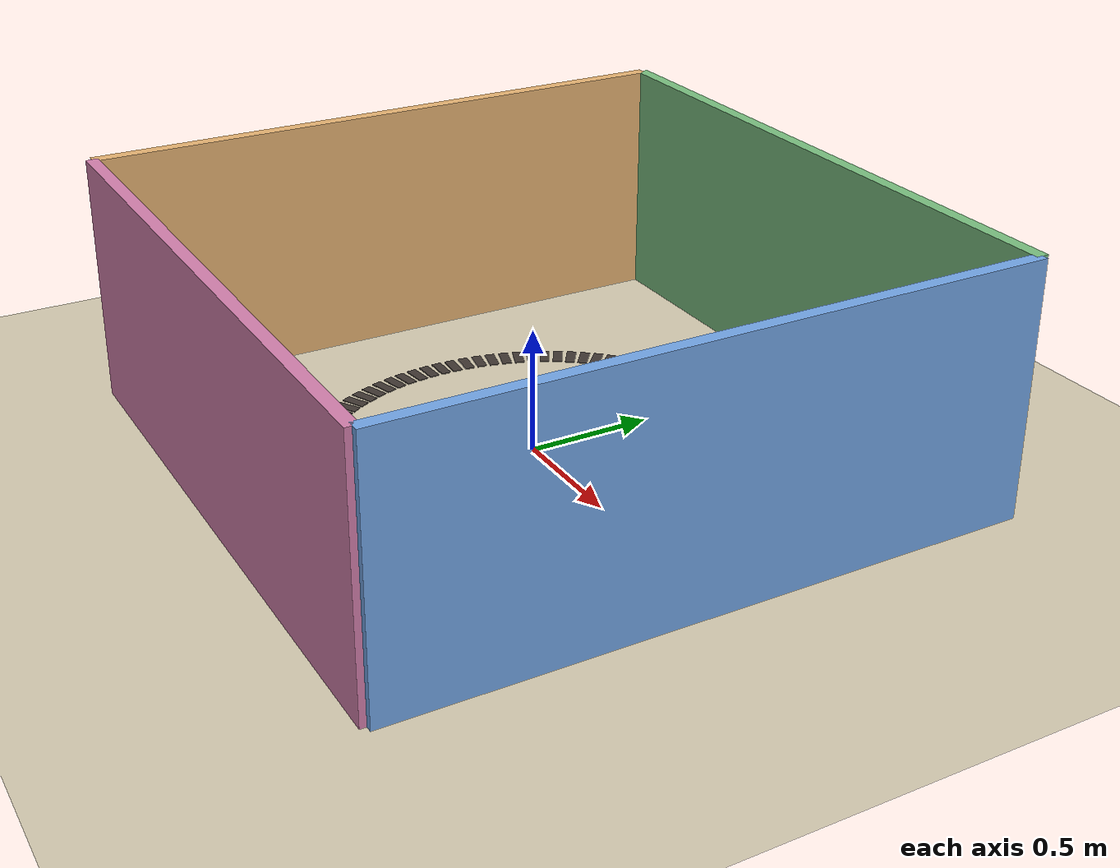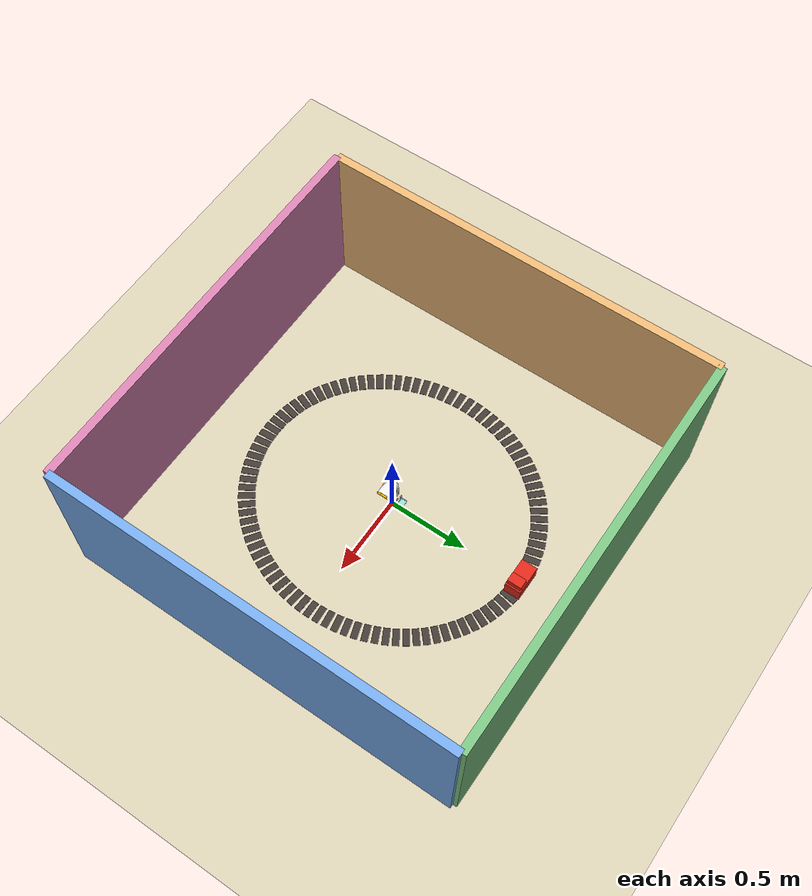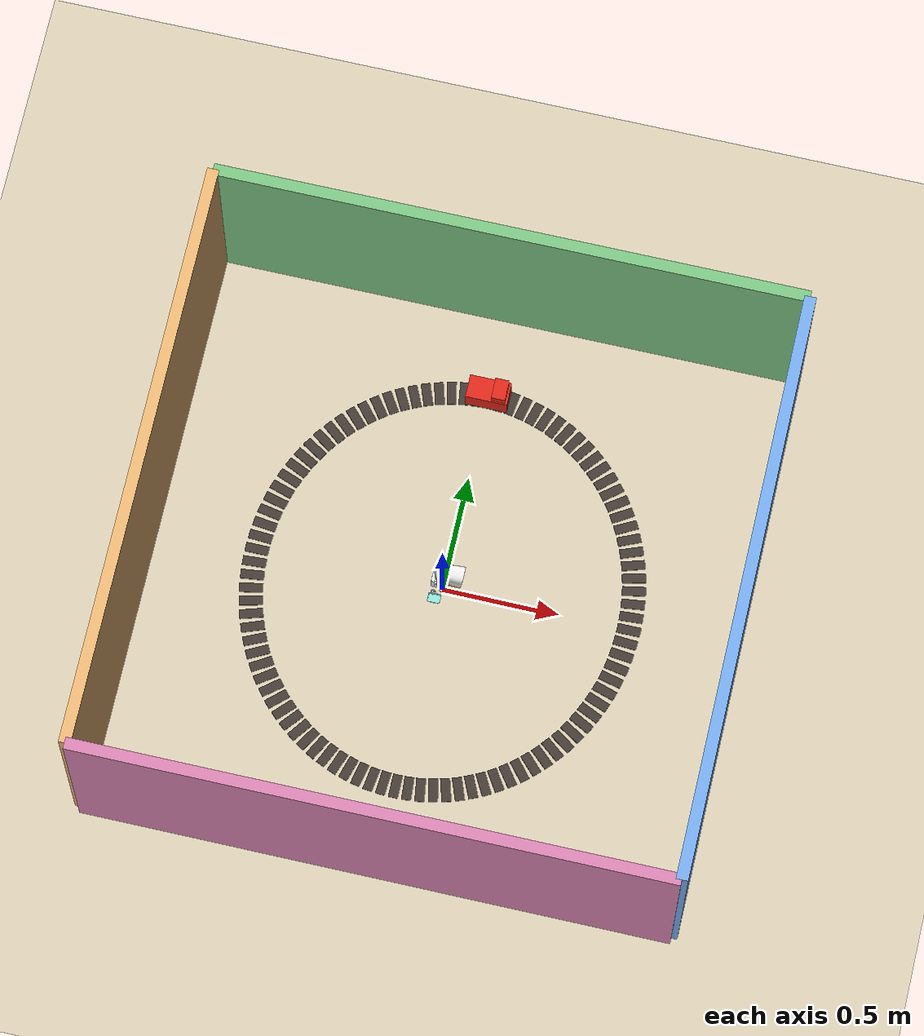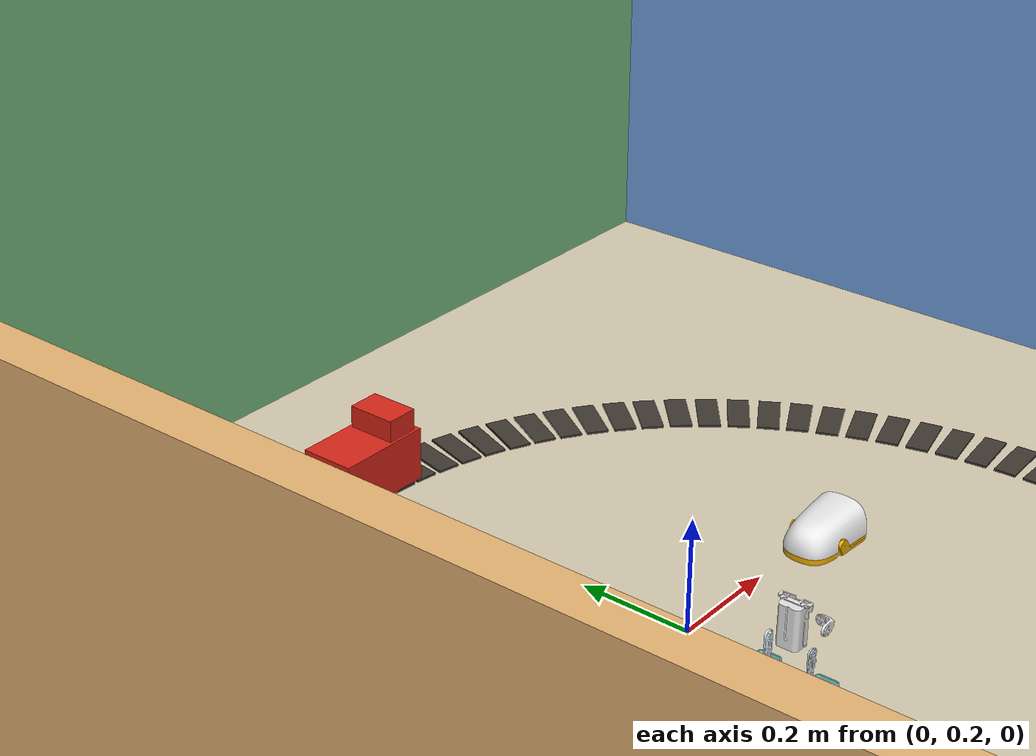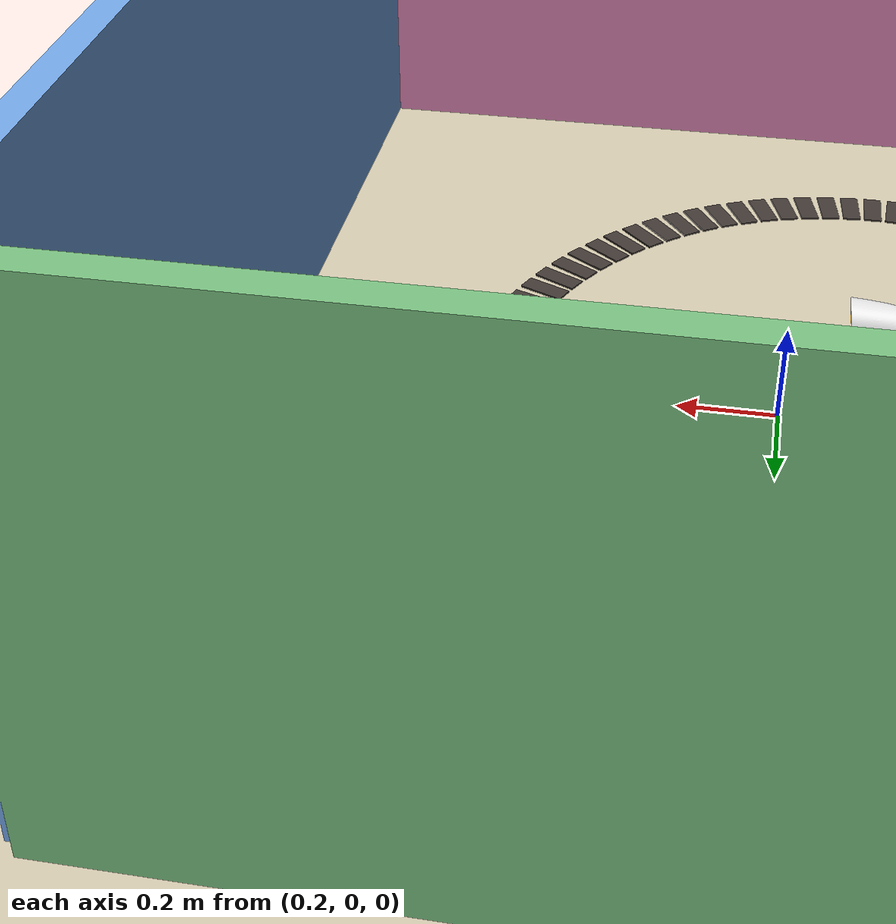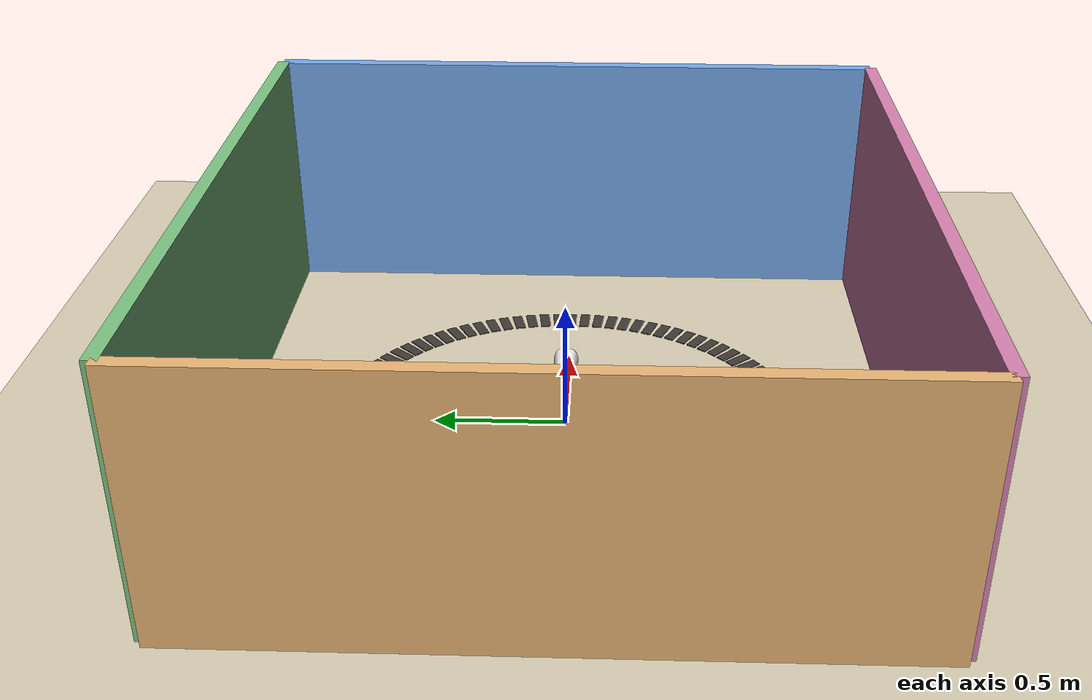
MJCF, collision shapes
<mujoco model="scene_playroom">
    <!-- GENERATED by mj_host/tools/playroom_gen.py --seed 1 --half 1.25
         --balls 0 --blocks 0 --chairs 0 --train.
         Do not edit by hand: regenerate. The manifest is beside this file. -->
    <include file="robot_overlay_playroom.xml" />
    <custom>
        <numeric name="train_path" data="0.0000 0.0000 0.8750 0.8000 1.5708"/>
        <numeric name="train_z" data="0.0500"/>
    </custom>

    <visual>
        <headlight diffuse="0.15 0.15 0.15" ambient="0.12 0.12 0.12" specular="0 0 0" />
        <rgba haze="0.9 0.92 0.95 1" />
        <global azimuth="160" elevation="-20" />
        <quality shadowsize="4096" />
        <map shadowscale="1.2" shadowclip="1.0" />
    </visual>

    <asset>
        <texture type="skybox" builtin="gradient" rgb1="0.85 0.9 1.0" rgb2="0.4 0.55 0.8" width="512" height="3072"/>
        <texture type="2d" name="floor_tex" builtin="checker" mark="edge" rgb1="0.86 0.82 0.72" rgb2="0.80 0.76 0.66" markrgb="0.7 0.66 0.58" width="256" height="256"/>
        <material name="floor_mat" texture="floor_tex" texuniform="true" texrepeat="8 8" reflectance="0.05"/>
        <texture type="2d" name="rug_tex" builtin="checker" mark="cross" rgb1="0.75 0.15 0.15" rgb2="0.95 0.75 0.2" markrgb="0.1 0.1 0.4" width="128" height="128"/>
        <material name="rug_mat" texture="rug_tex" texuniform="true" texrepeat="6 6"/>
        <texture type="2d" name="wall0_tex" builtin="checker" mark="random" random="0.08" rgb1="0.55 0.75 0.95" rgb2="0.35 0.55 0.85" markrgb="1 1 1" width="128" height="128"/>
        <material name="wall0_mat" texture="wall0_tex" texuniform="true" texrepeat="12 2"/>
        <texture type="2d" name="wall1_tex" builtin="checker" mark="random" random="0.08" rgb1="0.95 0.8 0.55" rgb2="0.85 0.6 0.35" markrgb="1 1 1" width="128" height="128"/>
        <material name="wall1_mat" texture="wall1_tex" texuniform="true" texrepeat="12 2"/>
        <texture type="2d" name="wall2_tex" builtin="checker" mark="random" random="0.08" rgb1="0.6 0.85 0.6" rgb2="0.35 0.65 0.4" markrgb="1 1 1" width="128" height="128"/>
        <material name="wall2_mat" texture="wall2_tex" texuniform="true" texrepeat="12 2"/>
        <texture type="2d" name="wall3_tex" builtin="checker" mark="random" random="0.08" rgb1="0.9 0.6 0.75" rgb2="0.75 0.4 0.6" markrgb="1 1 1" width="128" height="128"/>
        <material name="wall3_mat" texture="wall3_tex" texuniform="true" texrepeat="12 2"/>
        <texture type="2d" name="wood_tex" builtin="gradient" rgb1="0.55 0.35 0.2" rgb2="0.7 0.5 0.3" width="64" height="64"/>
        <material name="wood_mat" texture="wood_tex" texuniform="true" texrepeat="3 3"/>
        <texture type="2d" name="stripe_tex" builtin="checker" mark="none" rgb1="0.1 0.1 0.6" rgb2="0.95 0.95 0.95" width="64" height="64"/>
        <material name="stripe_mat" texture="stripe_tex" texuniform="true" texrepeat="1 6"/>
        <texture type="2d" name="dots_tex" builtin="flat" mark="random" random="0.25" rgb1="0.95 0.5 0.1" markrgb="0.1 0.1 0.1" width="64" height="64"/>
        <material name="dots_mat" texture="dots_tex" texuniform="true" texrepeat="4 4"/>
        <material name="ball0_mat" rgba="0.9 0.1 0.1 1"/>
        <material name="ball1_mat" rgba="0.1 0.4 0.95 1"/>
        <material name="ball2_mat" rgba="0.95 0.85 0.1 1"/>
        <material name="block0_mat" rgba="0.2 0.8 0.3 1"/>
        <material name="block1_mat" rgba="0.8 0.2 0.8 1"/>
        <material name="block2_mat" rgba="0.1 0.8 0.85 1"/>
        <material name="clock_face_mat" rgba="0.98 0.98 0.95 1"/>
        <material name="train_mat" rgba="0.85 0.15 0.10 1"/>
        <material name="sleeper_mat" rgba="0.25 0.22 0.20 1"/>
        <material name="clock_hand_mat" rgba="0.05 0.05 0.05 1"/>
    </asset>

    <worldbody>
        <light name="sun" pos="1.9 -1.5 3.0" dir="-0.55 0.45 -0.70" diffuse="0.75 0.72 0.66" specular="0.15 0.15 0.15" directional="true" castshadow="true" />
        <light name="fill" pos="-1.2 1.2 2.0" dir="0.4 -0.4 -0.8" diffuse="0.22 0.23 0.26" specular="0 0 0" directional="true" castshadow="false" />
        <geom name="floor" size="0 0 0.05" pos="0 0 0" type="plane" material="floor_mat"/>
        <geom name="wall_px" type="box" size="0.025 1.25 0.5" pos="1.25 0 0.5" material="wall0_mat"/>
        <geom name="wall_nx" type="box" size="0.025 1.25 0.5" pos="-1.25 0 0.5" material="wall1_mat"/>
        <geom name="wall_py" type="box" size="1.25 0.025 0.5" pos="0 1.25 0.5" material="wall2_mat"/>
        <geom name="wall_ny" type="box" size="1.25 0.025 0.5" pos="0 -1.25 0.5" material="wall3_mat"/>
        <geom name="track_sleeper0" type="box" size="0.02 0.05 0.002" pos="-0.000 0.875 0.002" euler="0 0 -3.142" material="sleeper_mat" contype="0" conaffinity="0"/>
        <geom name="track_sleeper1" type="box" size="0.02 0.05 0.002" pos="-0.052 0.873 0.002" euler="0 0 -3.070" material="sleeper_mat" contype="0" conaffinity="0"/>
        <geom name="track_sleeper2" type="box" size="0.02 0.05 0.002" pos="-0.104 0.868 0.002" euler="0 0 -2.999" material="sleeper_mat" contype="0" conaffinity="0"/>
        <geom name="track_sleeper3" type="box" size="0.02 0.05 0.002" pos="-0.156 0.858 0.002" euler="0 0 -2.927" material="sleeper_mat" contype="0" conaffinity="0"/>
        <geom name="track_sleeper4" type="box" size="0.02 0.05 0.002" pos="-0.207 0.845 0.002" euler="0 0 -2.857" material="sleeper_mat" contype="0" conaffinity="0"/>
        <geom name="track_sleeper5" type="box" size="0.02 0.05 0.002" pos="-0.257 0.829 0.002" euler="0 0 -2.786" material="sleeper_mat" contype="0" conaffinity="0"/>
        <geom name="track_sleeper6" type="box" size="0.02 0.05 0.002" pos="-0.306 0.808 0.002" euler="0 0 -2.716" material="sleeper_mat" contype="0" conaffinity="0"/>
        <geom name="track_sleeper7" type="box" size="0.02 0.05 0.002" pos="-0.354 0.785 0.002" euler="0 0 -2.647" material="sleeper_mat" contype="0" conaffinity="0"/>
        <geom name="track_sleeper8" type="box" size="0.02 0.05 0.002" pos="-0.400 0.758 0.002" euler="0 0 -2.578" material="sleeper_mat" contype="0" conaffinity="0"/>
        <geom name="track_sleeper9" type="box" size="0.02 0.05 0.002" pos="-0.444 0.728 0.002" euler="0 0 -2.510" material="sleeper_mat" contype="0" conaffinity="0"/>
        <geom name="track_sleeper10" type="box" size="0.02 0.05 0.002" pos="-0.487 0.694 0.002" euler="0 0 -2.443" material="sleeper_mat" contype="0" conaffinity="0"/>
        <geom name="track_sleeper11" type="box" size="0.02 0.05 0.002" pos="-0.527 0.658 0.002" euler="0 0 -2.377" material="sleeper_mat" contype="0" conaffinity="0"/>
        <geom name="track_sleeper12" type="box" size="0.02 0.05 0.002" pos="-0.566 0.619 0.002" euler="0 0 -2.311" material="sleeper_mat" contype="0" conaffinity="0"/>
        <geom name="track_sleeper13" type="box" size="0.02 0.05 0.002" pos="-0.601 0.577 0.002" euler="0 0 -2.247" material="sleeper_mat" contype="0" conaffinity="0"/>
        <geom name="track_sleeper14" type="box" size="0.02 0.05 0.002" pos="-0.635 0.533 0.002" euler="0 0 -2.183" material="sleeper_mat" contype="0" conaffinity="0"/>
        <geom name="track_sleeper15" type="box" size="0.02 0.05 0.002" pos="-0.665 0.486 0.002" euler="0 0 -2.119" material="sleeper_mat" contype="0" conaffinity="0"/>
        <geom name="track_sleeper16" type="box" size="0.02 0.05 0.002" pos="-0.693 0.437 0.002" euler="0 0 -2.056" material="sleeper_mat" contype="0" conaffinity="0"/>
        <geom name="track_sleeper17" type="box" size="0.02 0.05 0.002" pos="-0.717 0.387 0.002" euler="0 0 -1.994" material="sleeper_mat" contype="0" conaffinity="0"/>
        <geom name="track_sleeper18" type="box" size="0.02 0.05 0.002" pos="-0.739 0.335 0.002" euler="0 0 -1.933" material="sleeper_mat" contype="0" conaffinity="0"/>
        <geom name="track_sleeper19" type="box" size="0.02 0.05 0.002" pos="-0.758 0.281 0.002" euler="0 0 -1.872" material="sleeper_mat" contype="0" conaffinity="0"/>
        <geom name="track_sleeper20" type="box" size="0.02 0.05 0.002" pos="-0.773 0.226 0.002" euler="0 0 -1.811" material="sleeper_mat" contype="0" conaffinity="0"/>
        <geom name="track_sleeper21" type="box" size="0.02 0.05 0.002" pos="-0.785 0.171 0.002" euler="0 0 -1.751" material="sleeper_mat" contype="0" conaffinity="0"/>
        <geom name="track_sleeper22" type="box" size="0.02 0.05 0.002" pos="-0.793 0.114 0.002" euler="0 0 -1.691" material="sleeper_mat" contype="0" conaffinity="0"/>
        <geom name="track_sleeper23" type="box" size="0.02 0.05 0.002" pos="-0.798 0.057 0.002" euler="0 0 -1.631" material="sleeper_mat" contype="0" conaffinity="0"/>
        <geom name="track_sleeper24" type="box" size="0.02 0.05 0.002" pos="-0.800 -0.000 0.002" euler="0 0 -1.571" material="sleeper_mat" contype="0" conaffinity="0"/>
        <geom name="track_sleeper25" type="box" size="0.02 0.05 0.002" pos="-0.798 -0.057 0.002" euler="0 0 -1.511" material="sleeper_mat" contype="0" conaffinity="0"/>
        <geom name="track_sleeper26" type="box" size="0.02 0.05 0.002" pos="-0.793 -0.114 0.002" euler="0 0 -1.451" material="sleeper_mat" contype="0" conaffinity="0"/>
        <geom name="track_sleeper27" type="box" size="0.02 0.05 0.002" pos="-0.785 -0.171 0.002" euler="0 0 -1.391" material="sleeper_mat" contype="0" conaffinity="0"/>
        <geom name="track_sleeper28" type="box" size="0.02 0.05 0.002" pos="-0.773 -0.226 0.002" euler="0 0 -1.331" material="sleeper_mat" contype="0" conaffinity="0"/>
        <geom name="track_sleeper29" type="box" size="0.02 0.05 0.002" pos="-0.758 -0.281 0.002" euler="0 0 -1.270" material="sleeper_mat" contype="0" conaffinity="0"/>
        <geom name="track_sleeper30" type="box" size="0.02 0.05 0.002" pos="-0.739 -0.335 0.002" euler="0 0 -1.209" material="sleeper_mat" contype="0" conaffinity="0"/>
        <geom name="track_sleeper31" type="box" size="0.02 0.05 0.002" pos="-0.717 -0.387 0.002" euler="0 0 -1.147" material="sleeper_mat" contype="0" conaffinity="0"/>
        <geom name="track_sleeper32" type="box" size="0.02 0.05 0.002" pos="-0.693 -0.438 0.002" euler="0 0 -1.085" material="sleeper_mat" contype="0" conaffinity="0"/>
        <geom name="track_sleeper33" type="box" size="0.02 0.05 0.002" pos="-0.665 -0.486 0.002" euler="0 0 -1.022" material="sleeper_mat" contype="0" conaffinity="0"/>
        <geom name="track_sleeper34" type="box" size="0.02 0.05 0.002" pos="-0.635 -0.533 0.002" euler="0 0 -0.959" material="sleeper_mat" contype="0" conaffinity="0"/>
        <geom name="track_sleeper35" type="box" size="0.02 0.05 0.002" pos="-0.601 -0.577 0.002" euler="0 0 -0.895" material="sleeper_mat" contype="0" conaffinity="0"/>
        <geom name="track_sleeper36" type="box" size="0.02 0.05 0.002" pos="-0.566 -0.619 0.002" euler="0 0 -0.830" material="sleeper_mat" contype="0" conaffinity="0"/>
        <geom name="track_sleeper37" type="box" size="0.02 0.05 0.002" pos="-0.527 -0.658 0.002" euler="0 0 -0.765" material="sleeper_mat" contype="0" conaffinity="0"/>
        <geom name="track_sleeper38" type="box" size="0.02 0.05 0.002" pos="-0.487 -0.694 0.002" euler="0 0 -0.698" material="sleeper_mat" contype="0" conaffinity="0"/>
        <geom name="track_sleeper39" type="box" size="0.02 0.05 0.002" pos="-0.444 -0.728 0.002" euler="0 0 -0.631" material="sleeper_mat" contype="0" conaffinity="0"/>
        <geom name="track_sleeper40" type="box" size="0.02 0.05 0.002" pos="-0.400 -0.758 0.002" euler="0 0 -0.563" material="sleeper_mat" contype="0" conaffinity="0"/>
        <geom name="track_sleeper41" type="box" size="0.02 0.05 0.002" pos="-0.354 -0.785 0.002" euler="0 0 -0.495" material="sleeper_mat" contype="0" conaffinity="0"/>
        <geom name="track_sleeper42" type="box" size="0.02 0.05 0.002" pos="-0.306 -0.808 0.002" euler="0 0 -0.425" material="sleeper_mat" contype="0" conaffinity="0"/>
        <geom name="track_sleeper43" type="box" size="0.02 0.05 0.002" pos="-0.257 -0.829 0.002" euler="0 0 -0.355" material="sleeper_mat" contype="0" conaffinity="0"/>
        <geom name="track_sleeper44" type="box" size="0.02 0.05 0.002" pos="-0.207 -0.845 0.002" euler="0 0 -0.285" material="sleeper_mat" contype="0" conaffinity="0"/>
        <geom name="track_sleeper45" type="box" size="0.02 0.05 0.002" pos="-0.156 -0.858 0.002" euler="0 0 -0.214" material="sleeper_mat" contype="0" conaffinity="0"/>
        <geom name="track_sleeper46" type="box" size="0.02 0.05 0.002" pos="-0.104 -0.868 0.002" euler="0 0 -0.143" material="sleeper_mat" contype="0" conaffinity="0"/>
        <geom name="track_sleeper47" type="box" size="0.02 0.05 0.002" pos="-0.052 -0.873 0.002" euler="0 0 -0.072" material="sleeper_mat" contype="0" conaffinity="0"/>
        <geom name="track_sleeper48" type="box" size="0.02 0.05 0.002" pos="0.000 -0.875 0.002" euler="0 0 0.000" material="sleeper_mat" contype="0" conaffinity="0"/>
        <geom name="track_sleeper49" type="box" size="0.02 0.05 0.002" pos="0.052 -0.873 0.002" euler="0 0 0.072" material="sleeper_mat" contype="0" conaffinity="0"/>
        <geom name="track_sleeper50" type="box" size="0.02 0.05 0.002" pos="0.104 -0.868 0.002" euler="0 0 0.143" material="sleeper_mat" contype="0" conaffinity="0"/>
        <geom name="track_sleeper51" type="box" size="0.02 0.05 0.002" pos="0.156 -0.858 0.002" euler="0 0 0.214" material="sleeper_mat" contype="0" conaffinity="0"/>
        <geom name="track_sleeper52" type="box" size="0.02 0.05 0.002" pos="0.207 -0.845 0.002" euler="0 0 0.285" material="sleeper_mat" contype="0" conaffinity="0"/>
        <geom name="track_sleeper53" type="box" size="0.02 0.05 0.002" pos="0.257 -0.829 0.002" euler="0 0 0.356" material="sleeper_mat" contype="0" conaffinity="0"/>
        <geom name="track_sleeper54" type="box" size="0.02 0.05 0.002" pos="0.306 -0.808 0.002" euler="0 0 0.425" material="sleeper_mat" contype="0" conaffinity="0"/>
        <geom name="track_sleeper55" type="box" size="0.02 0.05 0.002" pos="0.354 -0.785 0.002" euler="0 0 0.495" material="sleeper_mat" contype="0" conaffinity="0"/>
        <geom name="track_sleeper56" type="box" size="0.02 0.05 0.002" pos="0.400 -0.758 0.002" euler="0 0 0.563" material="sleeper_mat" contype="0" conaffinity="0"/>
        <geom name="track_sleeper57" type="box" size="0.02 0.05 0.002" pos="0.444 -0.728 0.002" euler="0 0 0.631" material="sleeper_mat" contype="0" conaffinity="0"/>
        <geom name="track_sleeper58" type="box" size="0.02 0.05 0.002" pos="0.487 -0.694 0.002" euler="0 0 0.698" material="sleeper_mat" contype="0" conaffinity="0"/>
        <geom name="track_sleeper59" type="box" size="0.02 0.05 0.002" pos="0.527 -0.658 0.002" euler="0 0 0.765" material="sleeper_mat" contype="0" conaffinity="0"/>
        <geom name="track_sleeper60" type="box" size="0.02 0.05 0.002" pos="0.566 -0.619 0.002" euler="0 0 0.830" material="sleeper_mat" contype="0" conaffinity="0"/>
        <geom name="track_sleeper61" type="box" size="0.02 0.05 0.002" pos="0.601 -0.577 0.002" euler="0 0 0.895" material="sleeper_mat" contype="0" conaffinity="0"/>
        <geom name="track_sleeper62" type="box" size="0.02 0.05 0.002" pos="0.635 -0.533 0.002" euler="0 0 0.959" material="sleeper_mat" contype="0" conaffinity="0"/>
        <geom name="track_sleeper63" type="box" size="0.02 0.05 0.002" pos="0.665 -0.486 0.002" euler="0 0 1.022" material="sleeper_mat" contype="0" conaffinity="0"/>
        <geom name="track_sleeper64" type="box" size="0.02 0.05 0.002" pos="0.693 -0.437 0.002" euler="0 0 1.085" material="sleeper_mat" contype="0" conaffinity="0"/>
        <geom name="track_sleeper65" type="box" size="0.02 0.05 0.002" pos="0.717 -0.387 0.002" euler="0 0 1.147" material="sleeper_mat" contype="0" conaffinity="0"/>
        <geom name="track_sleeper66" type="box" size="0.02 0.05 0.002" pos="0.739 -0.335 0.002" euler="0 0 1.209" material="sleeper_mat" contype="0" conaffinity="0"/>
        <geom name="track_sleeper67" type="box" size="0.02 0.05 0.002" pos="0.758 -0.281 0.002" euler="0 0 1.270" material="sleeper_mat" contype="0" conaffinity="0"/>
        <geom name="track_sleeper68" type="box" size="0.02 0.05 0.002" pos="0.773 -0.226 0.002" euler="0 0 1.331" material="sleeper_mat" contype="0" conaffinity="0"/>
        <geom name="track_sleeper69" type="box" size="0.02 0.05 0.002" pos="0.785 -0.171 0.002" euler="0 0 1.391" material="sleeper_mat" contype="0" conaffinity="0"/>
        <geom name="track_sleeper70" type="box" size="0.02 0.05 0.002" pos="0.793 -0.114 0.002" euler="0 0 1.451" material="sleeper_mat" contype="0" conaffinity="0"/>
        <geom name="track_sleeper71" type="box" size="0.02 0.05 0.002" pos="0.798 -0.057 0.002" euler="0 0 1.511" material="sleeper_mat" contype="0" conaffinity="0"/>
        <geom name="track_sleeper72" type="box" size="0.02 0.05 0.002" pos="0.800 0.000 0.002" euler="0 0 1.571" material="sleeper_mat" contype="0" conaffinity="0"/>
        <geom name="track_sleeper73" type="box" size="0.02 0.05 0.002" pos="0.798 0.057 0.002" euler="0 0 1.631" material="sleeper_mat" contype="0" conaffinity="0"/>
        <geom name="track_sleeper74" type="box" size="0.02 0.05 0.002" pos="0.793 0.114 0.002" euler="0 0 1.691" material="sleeper_mat" contype="0" conaffinity="0"/>
        <geom name="track_sleeper75" type="box" size="0.02 0.05 0.002" pos="0.785 0.171 0.002" euler="0 0 1.751" material="sleeper_mat" contype="0" conaffinity="0"/>
        <geom name="track_sleeper76" type="box" size="0.02 0.05 0.002" pos="0.773 0.226 0.002" euler="0 0 1.811" material="sleeper_mat" contype="0" conaffinity="0"/>
        <geom name="track_sleeper77" type="box" size="0.02 0.05 0.002" pos="0.758 0.281 0.002" euler="0 0 1.872" material="sleeper_mat" contype="0" conaffinity="0"/>
        <geom name="track_sleeper78" type="box" size="0.02 0.05 0.002" pos="0.739 0.335 0.002" euler="0 0 1.933" material="sleeper_mat" contype="0" conaffinity="0"/>
        <geom name="track_sleeper79" type="box" size="0.02 0.05 0.002" pos="0.717 0.387 0.002" euler="0 0 1.994" material="sleeper_mat" contype="0" conaffinity="0"/>
        <geom name="track_sleeper80" type="box" size="0.02 0.05 0.002" pos="0.693 0.438 0.002" euler="0 0 2.056" material="sleeper_mat" contype="0" conaffinity="0"/>
        <geom name="track_sleeper81" type="box" size="0.02 0.05 0.002" pos="0.665 0.486 0.002" euler="0 0 2.119" material="sleeper_mat" contype="0" conaffinity="0"/>
        <geom name="track_sleeper82" type="box" size="0.02 0.05 0.002" pos="0.635 0.533 0.002" euler="0 0 2.183" material="sleeper_mat" contype="0" conaffinity="0"/>
        <geom name="track_sleeper83" type="box" size="0.02 0.05 0.002" pos="0.601 0.577 0.002" euler="0 0 2.247" material="sleeper_mat" contype="0" conaffinity="0"/>
        <geom name="track_sleeper84" type="box" size="0.02 0.05 0.002" pos="0.566 0.619 0.002" euler="0 0 2.311" material="sleeper_mat" contype="0" conaffinity="0"/>
        <geom name="track_sleeper85" type="box" size="0.02 0.05 0.002" pos="0.527 0.658 0.002" euler="0 0 2.377" material="sleeper_mat" contype="0" conaffinity="0"/>
        <geom name="track_sleeper86" type="box" size="0.02 0.05 0.002" pos="0.487 0.694 0.002" euler="0 0 2.443" material="sleeper_mat" contype="0" conaffinity="0"/>
        <geom name="track_sleeper87" type="box" size="0.02 0.05 0.002" pos="0.444 0.728 0.002" euler="0 0 2.510" material="sleeper_mat" contype="0" conaffinity="0"/>
        <geom name="track_sleeper88" type="box" size="0.02 0.05 0.002" pos="0.400 0.758 0.002" euler="0 0 2.578" material="sleeper_mat" contype="0" conaffinity="0"/>
        <geom name="track_sleeper89" type="box" size="0.02 0.05 0.002" pos="0.354 0.785 0.002" euler="0 0 2.647" material="sleeper_mat" contype="0" conaffinity="0"/>
        <geom name="track_sleeper90" type="box" size="0.02 0.05 0.002" pos="0.306 0.808 0.002" euler="0 0 2.716" material="sleeper_mat" contype="0" conaffinity="0"/>
        <geom name="track_sleeper91" type="box" size="0.02 0.05 0.002" pos="0.257 0.829 0.002" euler="0 0 2.786" material="sleeper_mat" contype="0" conaffinity="0"/>
        <geom name="track_sleeper92" type="box" size="0.02 0.05 0.002" pos="0.207 0.845 0.002" euler="0 0 2.857" material="sleeper_mat" contype="0" conaffinity="0"/>
        <geom name="track_sleeper93" type="box" size="0.02 0.05 0.002" pos="0.156 0.858 0.002" euler="0 0 2.927" material="sleeper_mat" contype="0" conaffinity="0"/>
        <geom name="track_sleeper94" type="box" size="0.02 0.05 0.002" pos="0.104 0.868 0.002" euler="0 0 2.999" material="sleeper_mat" contype="0" conaffinity="0"/>
        <geom name="track_sleeper95" type="box" size="0.02 0.05 0.002" pos="0.052 0.873 0.002" euler="0 0 3.070" material="sleeper_mat" contype="0" conaffinity="0"/>
        <body name="mov_train0" pos="-0.000 0.875 0.050" euler="0 0 3.142">
          <freejoint/>
          <geom name="mov_train0_geom" type="box" size="0.09 0.05 0.05" material="train_mat" mass="0.3" friction="0.6"/>
          <geom name="mov_train0_cab" type="box" size="0.03 0.045 0.02" pos="-0.050 0 0.070" material="train_mat" mass="0.03"/>
        </body>
    </worldbody>
    <keyframe>
        <key name="INIT" qpos="0 0 0.12 1 0 0 0 0 0 0 0 0 0 0 0 0 0 0 0 0 0 -0.000 0.875 0.050 -0.000002 0 0 1.000000" ctrl="0 0 0 0 0 0 0 0 0 0 0 0 0 0"/>
        <key name="STAND" qpos="0 0 0.12 1 0 0 0 0 -0.0873 -0.5236 0 0.5236 0.3491 -0.3491 0 0 0 0.0873 0.5236 0 -0.5236 -0.000 0.875 0.050 -0.000002 0 0 1.000000" ctrl="0 -0.0873 -0.5236 0 0.5236 0.3491 -0.3491 0 0 0 0.0873 0.5236 0 -0.5236"/>
        <key name="SIT" qpos="0 0 0.07 1 0 0 0 0 0 -0.5236 1.0472 0 0.5 1.6 0 0 0 0 0.5236 -1.0472 0 -0.000 0.875 0.050 -0.000002 0 0 1.000000" ctrl="0 0 -0.5236 1.0472 0 0.5 1.6 0 0 0 0 0.5236 -1.0472 0"/>
        <key name="FOLD" qpos="0 0 0.07 1 0 0 0 0 0 1.57 1.57 0 1 1 0 0 0 0 -1.57 -1.57 0 -0.000 0.875 0.050 -0.000002 0 0 1.000000" ctrl="0 0 1.57 1.57 0 1 1 0 0 0 0 -1.57 -1.57 0"/>
    </keyframe>
</mujoco>

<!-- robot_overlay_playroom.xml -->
<!-- GENERATED OVERLAY of robot_allcollisions.xml by mj_host/tools/playroom_gen.py: the vendored
     file with the head_camera line replaced (see CAMERA_LINE_NEW there). Do not edit; regenerate. -->
<!-- Generated using onshape-to-robot -->
<!-- Onshape https://cad.onshape.com/documents/804927696f06d877f3f1803e/w/5b75db19292e71970de02dee/e/ef6e972847fec8d82570b35e -->
<mujoco model="microduck">
  <compiler angle="radian" meshdir="assets" autolimits="true"/>
  <default>
    <default class="microduck">
      <joint frictionloss="0.1" armature="0.005"/>
      <position kp="50" dampratio="1"/>
      <default class="visual">
        <geom type="mesh" contype="0" conaffinity="0" group="2"/>
      </default>
      <default class="collision">
        <geom group="3"/>
      </default>
    </default>
  </default>
  <!-- Additional joints_properties.xml -->
  <default>
    <default class="perfect_actuator">
      <geom contype="0" conaffinity="0"/>
      <joint damping="0.15" frictionloss="0.1" armature="0.001"/>
      <position kp="10.0" kv="0.1" forcerange="-20.0 20.0"/>
    </default>
    <default class="chosen_actuator_old">
      <geom contype="0" conaffinity="0"/>
      <joint damping="0.048" frictionloss="0.006" armature="0.002"/>
      <position kp="0.52" kv="0.0" forcerange="-0.91 0.91" ctrlrange="-10.0 10.0"/>
    </default>
    <default class="chosen_actuator_new">
      <!-- removing contaminated data -->
      <geom contype="0" conaffinity="0"/>
      <joint damping="0.041" frictionloss="0.032" armature="0.002"/>
      <position kp="0.386" kv="0.0" forcerange="-0.67 0.67" ctrlrange="-10.0 10.0"/>
    </default>
    <default class="chosen_actuator_antoine">
      <geom contype="0" conaffinity="0"/>
      <joint damping="0.044" frictionloss="0.013" armature="0.0017"/>
      <position kp="0.43" kv="0.0" forcerange="-0.75 0.75" ctrlrange="-10.0 10.0"/>
    </default>
    <default class="chosen_actuator">
      <!-- marc -->
      <geom contype="0" conaffinity="0"/>
      <joint damping="0.053" frictionloss="0.0048" armature="0.0018"/>
      <!-- 200 kp -->
      <position kp="0.55" kv="0.0" forcerange="-0.96 0.96" ctrlrange="-10.0 10.0"/>
      <!-- 125 kp -->
    </default>
    <default class="passive_wheel">
      <geom contype="0" conaffinity="0"/>
      <joint damping="0.0" frictionloss="0.0" armature="0.0001"/>
    </default>
    <default class="passive_joint">
      <geom contype="0" conaffinity="0"/>
      <joint damping="0.0" frictionloss="0.0" armature="0.0001"/>
    </default>
  </default>
  <!-- Additional sensors.xml -->
  <sensor>
    <framequat name="orientation" objtype="site" noise="0.001" objname="imu"/>
    <gyro name="angular-velocity" site="imu" noise="0.005"/>
    <gyro name="imu_ang_vel" site="imu"/>
    <velocimeter name="imu_lin_vel" site="imu"/>
    <accelerometer name="imu_accel" site="imu"/>
    <gyro name="head_gyro" site="head_imu"/><!-- OVERLAY H0: the head IMU, as on the ToF board -->
    <framequat name="head_orientation" objtype="site" objname="head_imu"/>
    <subtreeangmom name="root_angmom" body="trunk_base"/>
  </sensor>
  <!-- Additional additional.xml -->
  <default>
    <default class="self_collision_only">
      <geom group="3" contype="2" conaffinity="2"/>
    </default>
    <equality solref="0.002 1" solimp="0.99 0.999 0.0005 0.5 2"/>
  </default>
  <!-- Jaw collision mesh overlaps the bottom head shell by ~2cm because the closed -->
  <!-- loop linkage positions it inside the head. Without these excludes the -->
  <!-- self-collision sensor reports a constant 2 contacts, giving a -->
  <!-- permanent ~-2.0 reward penalty in the standup env. -->
  <worldbody>
    <!-- Link trunk_base -->
    <body name="trunk_base" pos="0 0 0.12" quat="1 0 0 0" childclass="microduck">
      <freejoint name="trunk_base_freejoint"/>
      <inertial pos="-0.0226332 -2.70828e-05 0.00280064" mass="0.199224" fullinertia="0.000123975 0.000145931 0.000115351 7.1651e-08 -2.06915e-05 1.32429e-07"/>
      <!-- Part seeed_bearing__configuration__22x16x4 -->
      <geom type="mesh" class="visual" pos="0.006 0.0175 -0.005" quat="1 -0 -0 0" mesh="seeed_bearing__configuration__22x16x4" material="seeed_bearing__configuration__22x16x4_material"/>
      <!-- Part right_shell -->
      <geom type="mesh" class="visual" pos="0.004 -0.0005 -0.0175" quat="0.707107 -0 -0 0.707107" mesh="right_shell" material="right_shell_material"/>
      <!-- Part banana_pcb_locker -->
      <geom type="mesh" class="visual" pos="0.0042 -0 -0.0175215" quat="0.707107 -0 0 0.707107" mesh="banana_pcb_locker" material="banana_pcb_locker_material"/>
      <!-- Part trunk_base -->
      <geom type="mesh" class="visual" pos="0.004 -0 -0.0175" quat="0.707107 -0 -0 0.707107" mesh="trunk_base" material="trunk_base_material"/>
      <!-- Part xl330 -->
      <geom type="mesh" class="visual" pos="0.006 0.0175 0.0115" quat="0 0.707107 -0 0.707107" mesh="xl330" material="xl330_material"/>
      <!-- Part power_support -->
      <geom type="mesh" class="visual" pos="0.004 -0 -0.0175215" quat="0.707107 -0 0 0.707107" mesh="power_support" material="power_support_material"/>
      <geom type="mesh" class="self_collision_only" pos="0.004 -0 -0.0175215" quat="0.707107 -0 0 0.707107" mesh="power_support" material="power_support_material"/>
      <!-- Part np_f970 -->
      <geom type="mesh" class="visual" pos="-0.0359693 0 -0.00385049" quat="0.00617059 0.70708 -0.70708 -0.00617059" mesh="np_f970" material="np_f970_material"/>
      <geom type="mesh" class="collision" pos="-0.0359693 0 -0.00385049" quat="0.00617059 0.70708 -0.70708 -0.00617059" mesh="np_f970" material="np_f970_material"/>
      <!-- Part xl330_2 -->
      <geom type="mesh" class="visual" pos="0.006 -0.0175 0.0115" quat="0 0.707107 -0 0.707107" mesh="xl330" material="xl330_material"/>
      <!-- Part left_shell -->
      <geom type="mesh" class="visual" pos="0.004 -0 -0.0175785" quat="0.707107 0 -0 0.707107" mesh="left_shell" material="left_shell_material"/>
      <!-- Part seeed_bearing__configuration__22x16x4_2 -->
      <geom type="mesh" class="visual" pos="0.006 -0.0175 -0.005" quat="1 -0 -0 0" mesh="seeed_bearing__configuration__22x16x4" material="seeed_bearing__configuration__22x16x4_material"/>
      <!-- Frame imu -->
      <site group="3" name="imu" pos="-0.021 6.64098e-05 -0.0146984" quat="1 -0 -0 0"/>
      <!-- Link yaw2roll -->
      <body name="yaw2roll" pos="0.006 0.0175 -0.005" quat="0 -0.707107 -0.707107 -0">
        <!-- Joint from trunk_base to yaw2roll -->
        <joint axis="0 0 1" name="left_hip_yaw" type="hinge" range="-0.4363323129985824 0.5235987755982988" class="chosen_actuator"/>
        <inertial pos="-8.8e-11 0.00099414 0.0168917" mass="0.0230406" fullinertia="4.1964e-06 3.41752e-06 2.3265e-06 -0 -0 -5.0881e-08"/>
        <!-- Part yaw2roll -->
        <geom type="mesh" class="visual" pos="-0.0175 -0.002 0.0125" quat="0 1 0 0" mesh="yaw2roll" material="yaw2roll_material"/>
        <!-- Part xl330_3 -->
        <geom type="mesh" class="visual" pos="-0 0 0.0125" quat="0 -0.707107 0.707107 -0" mesh="xl330" material="xl330_material"/>
        <!-- Part seeed_bearing__configuration__22x16x4_3 -->
        <geom type="mesh" class="visual" pos="-0 0.0165 0.0125" quat="0.5 0.5 0.5 -0.5" mesh="seeed_bearing__configuration__22x16x4" material="seeed_bearing__configuration__22x16x4_material"/>
        <!-- Part bearing_roll -->
        <geom type="mesh" class="visual" pos="-0.0175 -0.002 0.0125" quat="0 -1 -0 -0" mesh="bearing_roll" material="bearing_roll_material"/>
        <!-- Link hip_l -->
        <body name="hip_l" pos="0 0.0165 0.0125" quat="0.707107 -0.707107 -0 -0">
          <!-- Joint from yaw2roll to hip_l -->
          <joint axis="0 0 1" name="left_hip_roll" type="hinge" range="-0.3839724354387525 0.3839724354387525" class="chosen_actuator"/>
          <inertial pos="0.014815 1.6179e-08 -0.00829992" mass="0.00618934" fullinertia="8.60626e-07 1.15753e-06 6.51588e-07 1e-12 3.89882e-07 -1e-12"/>
          <!-- Part seeed_bearing__configuration__22x16x4_4 -->
          <geom type="mesh" class="visual" pos="0.021 0 -0.0185" quat="0.5 0.5 0.5 0.5" mesh="seeed_bearing__configuration__22x16x4" material="seeed_bearing__configuration__22x16x4_material"/>
          <!-- Part hip_l -->
          <geom type="mesh" class="visual" pos="-0.0175 0 -0.0185" quat="0.707107 -0.707107 0 -0" mesh="hip_l" material="hip_l_material"/>
          <geom type="mesh" class="collision" pos="-0.0175 0 -0.0185" quat="0.707107 -0.707107 0 -0" mesh="hip_l" material="hip_l_material"/>
          <!-- Link upper_leg_left -->
          <body name="upper_leg_left" pos="0.025 0 -0.0185" quat="0.5 -0.5 0.5 -0.5">
            <!-- Joint from hip_l to upper_leg_left -->
            <joint axis="0 0 1" name="left_hip_pitch" type="hinge" range="-1.570796326795005 1.5707963267947882" class="chosen_actuator"/>
            <inertial pos="0.006766 0.0228838 0.0134531" mass="0.0482067" fullinertia="1.68753e-05 1.03691e-05 1.98269e-05 -4.41852e-06 2.27982e-07 3.89298e-07"/>
            <!-- Part upper_leg_left -->
            <geom type="mesh" class="visual" pos="-0 -0 -0.0425" quat="0.5 -0.5 -0.5 -0.5" mesh="upper_leg_left" material="upper_leg_left_material"/>
            <!-- Part xl330_4 -->
            <geom type="mesh" class="visual" pos="0.022 0.0357771 0.0125" quat="0 -0.707107 -0 -0.707107" mesh="xl330" material="xl330_material"/>
            <!-- Part upper_leg_rigidity_plate -->
            <geom type="mesh" class="visual" pos="0 -0 -0.0425" quat="0.5 -0.5 -0.5 -0.5" mesh="upper_leg_rigidity_plate" material="upper_leg_rigidity_plate_material"/>
            <!-- Part seeed_bearing__configuration__22x16x4_5 -->
            <geom type="mesh" class="visual" pos="0.022 0.0357771 -0.004" quat="0 0 0 1" mesh="seeed_bearing__configuration__22x16x4" material="seeed_bearing__configuration__22x16x4_material"/>
            <!-- Part xl330_5 -->
            <geom type="mesh" class="visual" pos="-0 -0 0.0125" quat="0.5 0.5 -0.5 0.5" mesh="xl330" material="xl330_material"/>
            <!-- Link leg -->
            <body name="leg" pos="0.022 0.0357771 -0.004" quat="0 0.707107 0.707107 0">
              <!-- Joint from upper_leg_left to leg -->
              <joint axis="0 0 1" name="left_knee" type="hinge" range="-1.570796326795012 1.570796326794781" class="chosen_actuator"/>
              <inertial pos="-1.52e-10 0.0318937 -0.00953505" mass="0.0215844" fullinertia="5.25056e-06 2.15507e-06 4.33925e-06 -1e-12 0 7.65005e-07"/>
              <!-- Part leg -->
              <geom type="mesh" class="visual" pos="-0.022 0.0357771 0.0385" quat="0.5 0.5 0.5 -0.5" mesh="leg" material="leg_material"/>
              <geom type="mesh" class="collision" pos="-0.022 0.0357771 0.0385" quat="0.5 0.5 0.5 -0.5" mesh="leg" material="leg_material"/>
              <!-- Part xl330_6 -->
              <geom type="mesh" class="visual" pos="0 0.042 -0.0115" quat="0.5 -0.5 -0.5 -0.5" mesh="xl330" material="xl330_material"/>
              <!-- Link ankle_left -->
              <body name="ankle_left" pos="0 0.042 -0.026" quat="0 1 -0 0">
                <!-- Joint from leg to ankle_left -->
                <joint axis="0 0 1" name="left_ankle" type="hinge" range="-1.5707963267949019 1.5707963267948912" class="chosen_actuator"/>
                <inertial pos="-0.00615738 -0.0137483 -0.0156586" mass="0.0300246" fullinertia="5.91525e-06 1.11534e-05 7.74015e-06 -2.0535e-07 8.2152e-08 5.6714e-08"/>
                <!-- Part sole_left -->
                <geom type="mesh" class="visual" pos="-0.022 0.00622291 -0.0647" quat="0.5 -0.5 -0.5 -0.5" mesh="sole_left" material="sole_left_material"/>
                <geom type="mesh" name="left_foot_collision" class="collision" pos="-0.022 0.00622291 -0.0647" quat="0.5 -0.5 -0.5 -0.5" mesh="sole_left" material="sole_left_material"/>
                <!-- Part foot_left -->
                <geom type="mesh" class="visual" pos="-0.022 0.00622291 -0.0647" quat="0.5 -0.5 -0.5 -0.5" mesh="foot_left" material="foot_left_material"/>
                <!-- Part seeed_bearing__configuration_default -->
                <geom type="mesh" class="visual" pos="0 0 -0.0322" quat="0 0 -0 1" mesh="seeed_bearing__configuration_default" material="seeed_bearing__configuration_default_material"/>
                <!-- Part ankle_left -->
                <geom type="mesh" class="visual" pos="-0.022 0.00622291 -0.0647" quat="0.5 -0.5 -0.5 -0.5" mesh="ankle_left" material="ankle_left_material"/>
                <!-- Frame left_foot -->
                <site group="3" name="left_foot" pos="-0 -0.0238146 -0.0140852" quat="0 0 0.707107 0.707107"/>
              </body>
            </body>
          </body>
        </body>
      </body>
      <!-- Link neck -->
      <body name="neck" pos="0.026 0.0145 0.0324215" quat="0 0 0.707107 -0.707107">
        <!-- Joint from trunk_base to neck -->
        <joint axis="0 0 1" name="neck_pitch" type="hinge" range="-1.5707963267948966 1.0471975511965976" class="chosen_actuator"/>
        <inertial pos="0 -0.025 0.0141665" mass="0.0368414" fullinertia="1.72925e-05 3.12694e-06 1.63707e-05 0 0 0"/>
        <!-- Part neck -->
        <geom type="mesh" class="visual" pos="0.022 0.05 0.028" quat="0.5 0.5 0.5 -0.5" mesh="neck" material="neck_material"/>
        <!-- Part xl330_7 -->
        <geom type="mesh" class="visual" pos="0 0 0.0145" quat="0.5 -0.5 -0.5 -0.5" mesh="xl330" material="xl330_material"/>
        <!-- Part xl330_8 -->
        <geom type="mesh" class="visual" pos="0 -0.05 0.0145" quat="0.5 0.5 -0.5 0.5" mesh="xl330" material="xl330_material"/>
        <!-- Part neck_2 -->
        <geom type="mesh" class="visual" pos="0.022 0.05 0.003" quat="0.5 0.5 0.5 -0.5" mesh="neck" material="neck_material"/>
        <!-- Link neck_pitch -->
        <body name="neck_pitch" pos="0 -0.05 -0" quat="0 1 0 0">
          <!-- Joint from neck to neck_pitch -->
          <joint axis="0 0 1" name="head_pitch" type="hinge" range="-1.5707963267948974 1.5707963267948957" class="chosen_actuator"/>
          <inertial pos="-6.533e-09 0.0116641 -0.0145" mass="0.00572" fullinertia="1.09186e-06 9.66855e-07 5.12111e-07 0 0 0"/>
          <!-- Part neck_pitch -->
          <geom type="mesh" class="visual" pos="-0 0.0287931 -0.0145" quat="0.5 -0.5 -0.5 -0.5" mesh="neck_pitch" material="neck_pitch_material"/>
          <!-- Part seeed_bearing__configuration__22x16x4_6 -->
          <geom type="mesh" class="visual" pos="-0 0.0207931 -0.0145" quat="0.707107 0.707107 0 0" mesh="seeed_bearing__configuration__22x16x4" material="seeed_bearing__configuration__22x16x4_material"/>
          <!-- Link yaw_roll_motion -->
          <body name="yaw_roll_motion" pos="-0 0.0186931 -0.0145" quat="0 0 -0.707107 -0.707107">
            <!-- Joint from neck_pitch to yaw_roll_motion -->
            <joint axis="0 0 1" name="head_yaw" type="hinge" range="-2.967059728390373 2.967059728390348" class="chosen_actuator"/>
            <inertial pos="-0.000166657 -0.00500964 0.0178065" mass="0.0486" fullinertia="6.97903e-06 8.10293e-06 9.57884e-06 3.21657e-07 -3.4797e-08 3.4295e-07"/>
            <!-- Part yaw_roll_motion -->
            <geom type="mesh" class="visual" pos="0 0 0.01" quat="0.707107 0 -0 0.707107" mesh="yaw_roll_motion" material="yaw_roll_motion_material"/>
            <!-- Part xl330_9 -->
            <geom type="mesh" class="visual" pos="0 0 0.0145" quat="0.5 -0.5 -0.5 -0.5" mesh="xl330" material="xl330_material"/>
            <!-- Part seeed_bearing__configuration__22x16x4_7 -->
            <geom type="mesh" class="visual" pos="-0.016 0 0.0145" quat="0.707107 -0 -0.707107 -0" mesh="seeed_bearing__configuration__22x16x4" material="seeed_bearing__configuration__22x16x4_material"/>
            <!-- Part seeed_bearing__configuration__22x16x4_8 -->
            <geom type="mesh" class="visual" pos="0.018 0 0.0145" quat="0.707107 -0 -0.707107 -0" mesh="seeed_bearing__configuration__22x16x4" material="seeed_bearing__configuration__22x16x4_material"/>
            <!-- Link jaw_soft -->
            <body name="jaw_soft" pos="-0.0179 0 0.0145" quat="0.707107 -0 -0.707107 -0">
              <!-- Joint from yaw_roll_motion to jaw_soft -->
              <joint axis="0 0 1" name="head_roll" type="hinge" range="-0.43633231299859127 0.4363323129985735" class="chosen_actuator"/>
              <inertial pos="0.00460523 0.00120047 -0.0324761" mass="0.188766" fullinertia="0.000320812 0.0002541 0.000149882 -6.32292e-07 6.57154e-06 4.18476e-06"/>
              <!-- Part lens -->
              <geom type="mesh" class="visual" pos="0.0155 -9.13778e-05 -0.05548" quat="0.5 -0.5 0.5 -0.5" mesh="lens" material="lens_material"/>
              <!-- Part face_part -->
              <geom type="mesh" class="visual" pos="-0.0045 -9.13778e-05 -0.0178" quat="0.5 0.5 0.5 0.5" mesh="face_part" material="face_part_material"/>
              <!-- Part xl330_10 -->
              <geom type="mesh" class="visual" pos="0.003 0.0255 -0.018" quat="0.707107 0 -0 -0.707107" mesh="xl330" material="xl330_material"/>
              <!-- Part jaw_soft -->
              <geom type="mesh" class="visual" pos="-0.0046 0 -0.0179996" quat="0.5 0.5 0.5 0.5" mesh="jaw_soft" material="jaw_soft_material"/>
              <!-- Part motor_support -->
              <geom type="mesh" class="visual" pos="-0.0045 0 -0.018" quat="0.5 0.5 0.5 0.5" mesh="motor_support" material="motor_support_material"/>
              <!-- Part top_head_shell -->
              <geom type="mesh" class="visual" pos="-0.0045 -0 -0.018" quat="0.5 0.5 0.5 0.5" mesh="top_head_shell" material="top_head_shell_material"/>
              <geom type="mesh" class="collision" pos="-0.0045 -0 -0.018" quat="0.5 0.5 0.5 0.5" mesh="top_head_shell" material="top_head_shell_material"/>
              <!-- Part xl330_11 -->
              <geom type="mesh" class="visual" pos="0 0 0.0145" quat="0.5 -0.5 -0.5 -0.5" mesh="xl330" material="xl330_material"/>
              <!-- Part seeed_bearing__configuration_default_2 -->
              <geom type="mesh" class="visual" pos="0.0032 -0.04 -0.018" quat="0.5 -0.5 0.5 0.5" mesh="seeed_bearing__configuration_default" material="seeed_bearing__configuration_default_material"/>
              <!-- Part elec_rpi_robot_hat_pcb -->
              <geom type="mesh" class="visual" pos="0.02694 0.0289936 -0.0519" quat="0.707107 0 0 -0.707107" mesh="elec_rpi_robot_hat_pcb" material="elec_rpi_robot_hat_pcb_material"/>
              <!-- Part soft_mouth_top -->
              <geom type="mesh" class="visual" pos="-0.00420071 1.7776e-08 -0.0180814" quat="0.5 0.5 0.5 0.5" mesh="soft_mouth_top" material="soft_mouth_top_material"/>
              <!-- Part noenoeil -->
              <geom type="mesh" class="visual" pos="-0.0045 -9.13778e-05 -0.0178" quat="0.5 0.5 0.5 0.5" mesh="noenoeil" material="noenoeil_material"/>
              <!-- Part jaw -->
              <geom type="mesh" class="visual" pos="-0.0045 0 -0.018" quat="0.5 0.5 0.5 0.5" mesh="jaw" material="jaw_material"/>
              <geom type="mesh" class="collision" pos="-0.0045 0 -0.018" quat="0.5 0.5 0.5 0.5" mesh="jaw" material="jaw_material"/>
              <!-- Part bottom_head_shell -->
              <geom type="mesh" class="visual" pos="-0.0043 -0 -0.018" quat="0.5 0.5 0.5 0.5" mesh="bottom_head_shell" material="bottom_head_shell_material"/>
              <geom type="mesh" class="collision" pos="-0.0043 -0 -0.018" quat="0.5 0.5 0.5 0.5" mesh="bottom_head_shell" material="bottom_head_shell_material"/>
              <!-- Part m12_lens_holder -->
              <geom type="mesh" class="visual" pos="0.0155 -9.13778e-05 -0.05558" quat="0.5 -0.5 0.5 -0.5" mesh="m12_lens_holder" material="m12_lens_holder_material"/>
              <!-- Part pcb__raspberry_pi_zero_2_w -->
              <geom type="mesh" class="visual" pos="0.015435 -1.13778e-05 -0.06001" quat="0.5 -0.5 -0.5 0.5" mesh="pcb__raspberry_pi_zero_2_w" material="pcb__raspberry_pi_zero_2_w_material"/>
              <!-- Part speaker -->
              <geom type="mesh" class="visual" pos="0.01 -0.016786 0.0260226" quat="0.5 0.5 0.5 0.5" mesh="speaker" material="speaker_material"/>
              <!-- Frame head_camera -->
              <site group="3" name="head_camera" pos="0.0155 -9.13778e-05 -0.0733" quat="0.707107 0 0.707107 -0"/>
              <camera name="head_camera" pos="0.0155 -9.0e-05 -0.0818" quat="0.707107 0 0 -0.707107" fovy="49"/><!-- OVERLAY: re-placed at the lens front, facing the ToF forward, upright; see playroom_gen.py -->
              <!-- Frame tof -->
              <site group="3" name="tof" pos="0.0135 0.0224086 -0.0733" quat="0.707107 0 0.707107 -0"/>
              <!-- Frame head_imu -->
              <site group="3" name="head_imu" pos="0.0152323 0.000111069 -0.05106" quat="1 0 0 -0"/>
              <!-- Frame mouth_tip -->
              <site group="3" name="mouth_tip" pos="-0.00809334 -0 -0.0777383" quat="0.704015 0 0.710185 -0"/>
            </body>
          </body>
        </body>
      </body>
      <!-- Link bearing_roll -->
      <body name="bearing_roll" pos="0.006 -0.0175 -0.005" quat="0 0.707107 0.707107 0">
        <!-- Joint from trunk_base to bearing_roll -->
        <joint axis="0 0 1" name="right_hip_yaw" type="hinge" range="-0.5235987755982988 0.4363323129985824" class="chosen_actuator"/>
        <inertial pos="-8.8e-11 0.00099414 0.0168917" mass="0.0230406" fullinertia="4.1964e-06 3.41752e-06 2.3265e-06 -0 -0 -5.0881e-08"/>
        <!-- Part yaw2roll_2 -->
        <geom type="mesh" class="visual" pos="-0.0175 -0.002 0.0125" quat="0 1 0 0" mesh="yaw2roll" material="yaw2roll_material"/>
        <!-- Part xl330_12 -->
        <geom type="mesh" class="visual" pos="-0 0 0.0125" quat="0 -0.707107 0.707107 -0" mesh="xl330" material="xl330_material"/>
        <!-- Part bearing_roll_2 -->
        <geom type="mesh" class="visual" pos="-0.0175 -0.002 0.0125" quat="0 -1 -0 -0" mesh="bearing_roll" material="bearing_roll_material"/>
        <!-- Part seeed_bearing__configuration__22x16x4_9 -->
        <geom type="mesh" class="visual" pos="-0 0.0165 0.0125" quat="0.5 0.5 0.5 -0.5" mesh="seeed_bearing__configuration__22x16x4" material="seeed_bearing__configuration__22x16x4_material"/>
        <!-- Link hip_l_2 -->
        <body name="hip_l_2" pos="-0 0.0165 0.0125" quat="0 -0 0.707107 0.707107">
          <!-- Joint from bearing_roll to hip_l_2 -->
          <joint axis="0 0 1" name="right_hip_roll" type="hinge" range="-0.3839724354387525 0.3839724354387525" class="chosen_actuator"/>
          <inertial pos="0.014815 1.6212e-08 -0.00829992" mass="0.00618934" fullinertia="8.60626e-07 1.15753e-06 6.51588e-07 1e-12 3.89882e-07 -1e-12"/>
          <!-- Part hip_l_2 -->
          <geom type="mesh" class="visual" pos="-0.0175 0 -0.0185" quat="0.707107 -0.707107 -0 -0" mesh="hip_l" material="hip_l_material"/>
          <geom type="mesh" class="collision" pos="-0.0175 0 -0.0185" quat="0.707107 -0.707107 -0 -0" mesh="hip_l" material="hip_l_material"/>
          <!-- Part seeed_bearing__configuration__22x16x4_10 -->
          <geom type="mesh" class="visual" pos="0.025 0 -0.0185" quat="0.5 0.5 -0.5 -0.5" mesh="seeed_bearing__configuration__22x16x4" material="seeed_bearing__configuration__22x16x4_material"/>
          <!-- Link upper_leg_right -->
          <body name="upper_leg_right" pos="0.025 0 -0.0185" quat="0.5 -0.5 0.5 -0.5">
            <!-- Joint from hip_l_2 to upper_leg_right -->
            <joint axis="0 0 1" name="right_hip_pitch" type="hinge" range="-1.5707963267949268 1.5707963267948664" class="chosen_actuator"/>
            <inertial pos="-0.006766 0.0228838 0.0134531" mass="0.0482067" fullinertia="1.68753e-05 1.03691e-05 1.98269e-05 4.41852e-06 -2.27982e-07 3.89298e-07"/>
            <!-- Part xl330_13 -->
            <geom type="mesh" class="visual" pos="-0.022 0.0357771 0.0125" quat="0.707107 -0 -0.707107 -0" mesh="xl330" material="xl330_material"/>
            <!-- Part seeed_bearing__configuration__22x16x4_11 -->
            <geom type="mesh" class="visual" pos="-0.022 0.0357771 0" quat="0 1 -0 -0" mesh="seeed_bearing__configuration__22x16x4" material="seeed_bearing__configuration__22x16x4_material"/>
            <!-- Part upper_leg_rigidity_plate_2 -->
            <geom type="mesh" class="visual" pos="0 0 0.0435" quat="0.5 -0.5 0.5 0.5" mesh="upper_leg_rigidity_plate" material="upper_leg_rigidity_plate_material"/>
            <!-- Part upper_leg_right -->
            <geom type="mesh" class="visual" pos="-0 0 -0.0425" quat="0.5 -0.5 0.5 0.5" mesh="upper_leg_right" material="upper_leg_right_material"/>
            <!-- Part xl330_14 -->
            <geom type="mesh" class="visual" pos="0 0 0.0125" quat="0.5 0.5 -0.5 0.5" mesh="xl330" material="xl330_material"/>
            <!-- Link leg_2 -->
            <body name="leg_2" pos="-0.022 0.0357771 -0.004" quat="0 1 -0 -0">
              <!-- Joint from upper_leg_right to leg_2 -->
              <joint axis="0 0 1" name="right_knee" type="hinge" range="-1.570796326794932 1.570796326794861" class="chosen_actuator"/>
              <inertial pos="-0.0318937 -1.52e-10 -0.00953505" mass="0.0215844" fullinertia="2.15507e-06 5.25056e-06 4.33925e-06 1e-12 -7.65005e-07 0"/>
              <!-- Part xl330_15 -->
              <geom type="mesh" class="visual" pos="-0.042 0 -0.0115" quat="0.707107 -0 -0.707107 -0" mesh="xl330" material="xl330_material"/>
              <!-- Part leg_2 -->
              <geom type="mesh" class="visual" pos="-0.0357771 -0.022 0.0385" quat="0.707107 0 0.707107 -0" mesh="leg" material="leg_material"/>
              <geom type="mesh" class="collision" pos="-0.0357771 -0.022 0.0385" quat="0.707107 0 0.707107 -0" mesh="leg" material="leg_material"/>
              <!-- Link ankle_right -->
              <body name="ankle_right" pos="-0.042 0 -0.026" quat="0 -0.707107 -0.707107 0">
                <!-- Joint from leg_2 to ankle_right -->
                <joint axis="0 0 1" name="right_ankle" type="hinge" range="-1.5707963267949054 1.5707963267948877" class="chosen_actuator"/>
                <inertial pos="0.00615539 -0.0137482 -0.0156566" mass="0.0300251" fullinertia="5.91534e-06 1.11534e-05 7.74016e-06 2.04877e-07 -8.247e-08 5.7017e-08"/>
                <!-- Part ankle_right -->
                <geom type="mesh" class="visual" pos="0.022 0.00622291 -0.0647" quat="0.5 -0.5 0.5 0.5" mesh="ankle_right" material="ankle_right_material"/>
                <!-- Part sole_right -->
                <geom type="mesh" class="visual" pos="0.022 0.00622291 -0.0647" quat="0.5 -0.5 0.5 0.5" mesh="sole_right" material="sole_right_material"/>
                <geom type="mesh" name="right_foot_collision" class="collision" pos="0.022 0.00622291 -0.0647" quat="0.5 -0.5 0.5 0.5" mesh="sole_right" material="sole_right_material"/>
                <!-- Part seeed_bearing__configuration_default_3 -->
                <geom type="mesh" class="visual" pos="-0 0 -0.0292" quat="0 1 -0 -0" mesh="seeed_bearing__configuration_default" material="seeed_bearing__configuration_default_material"/>
                <!-- Part foot_right -->
                <geom type="mesh" class="visual" pos="0.022 0.00622291 -0.0647" quat="0.5 -0.5 0.5 0.5" mesh="foot_right" material="foot_right_material"/>
                <!-- Frame right_foot -->
                <site group="3" name="right_foot" pos="0 -0.0238146 -0.0140852" quat="0.707107 -0.707107 0 0"/>
              </body>
            </body>
          </body>
        </body>
      </body>
    </body>
  </worldbody>
  <asset>
    <mesh file="seeed_bearing__configuration__22x16x4.stl"/>
    <mesh file="sole_left.stl"/>
    <mesh file="yaw2roll.stl"/>
    <mesh file="sole_right.stl"/>
    <mesh file="leg.stl"/>
    <mesh file="xl330.stl"/>
    <mesh file="noenoeil.stl"/>
    <mesh file="pcb__raspberry_pi_zero_2_w.stl"/>
    <mesh file="neck_pitch.stl"/>
    <mesh file="foot_left.stl"/>
    <mesh file="ankle_left.stl"/>
    <mesh file="yaw_roll_motion.stl"/>
    <mesh file="left_shell.stl"/>
    <mesh file="m12_lens_holder.stl"/>
    <mesh file="jaw_soft.stl"/>
    <mesh file="elec_rpi_robot_hat_pcb.stl"/>
    <mesh file="top_head_shell.stl"/>
    <mesh file="lens.stl"/>
    <mesh file="bottom_head_shell.stl"/>
    <mesh file="motor_support.stl"/>
    <mesh file="neck.stl"/>
    <mesh file="np_f970.stl"/>
    <mesh file="upper_leg_rigidity_plate.stl"/>
    <mesh file="seeed_bearing__configuration_default.stl"/>
    <mesh file="soft_mouth_top.stl"/>
    <mesh file="trunk_base.stl"/>
    <mesh file="hip_l.stl"/>
    <mesh file="bearing_roll.stl"/>
    <mesh file="banana_pcb_locker.stl"/>
    <mesh file="speaker.stl"/>
    <mesh file="ankle_right.stl"/>
    <mesh file="upper_leg_right.stl"/>
    <mesh file="right_shell.stl"/>
    <mesh file="face_part.stl"/>
    <mesh file="foot_right.stl"/>
    <mesh file="power_support.stl"/>
    <mesh file="upper_leg_left.stl"/>
    <mesh file="jaw.stl"/>
    <material name="seeed_bearing__configuration__22x16x4_material" rgba="0.713725 0.760784 0.8 1"/>
    <material name="right_shell_material" rgba="0.8 0.8 0.8 1"/>
    <material name="banana_pcb_locker_material" rgba="0.647059 0.647059 0.647059 1"/>
    <material name="trunk_base_material" rgba="0.34902 0.376471 0.4 1"/>
    <material name="xl330_material" rgba="0.286275 0.286275 0.286275 1"/>
    <material name="power_support_material" rgba="0.901961 0.901961 0.901961 1"/>
    <material name="np_f970_material" rgba="0.901961 0.901961 0.901961 1"/>
    <material name="left_shell_material" rgba="0.8 0.8 0.8 1"/>
    <material name="yaw2roll_material" rgba="0.647059 0.647059 0.647059 1"/>
    <material name="bearing_roll_material" rgba="0.262745 0.282353 0.301961 1"/>
    <material name="hip_l_material" rgba="0.901961 0.901961 0.901961 1"/>
    <material name="upper_leg_left_material" rgba="0.866667 0.866667 0.866667 1"/>
    <material name="upper_leg_rigidity_plate_material" rgba="0.537255 0.854902 0.827451 1"/>
    <material name="leg_material" rgba="0.811765 0.858824 0.898039 1"/>
    <material name="sole_left_material" rgba="0.537255 0.854902 0.827451 1"/>
    <material name="foot_left_material" rgba="0.980392 0.713725 0.00392157 1"/>
    <material name="seeed_bearing__configuration_default_material" rgba="0.713725 0.760784 0.8 1"/>
    <material name="ankle_left_material" rgba="0.980392 0.713725 0.00392157 1"/>
    <material name="neck_material" rgba="0.8 0.8 0.8 1"/>
    <material name="neck_pitch_material" rgba="0.34902 0.376471 0.4 1"/>
    <material name="yaw_roll_motion_material" rgba="0.768627 0.886275 0.952941 1"/>
    <material name="lens_material" rgba="0.262745 0.282353 0.301961 1"/>
    <material name="face_part_material" rgba="0.34902 0.376471 0.4 1"/>
    <material name="jaw_soft_material" rgba="0.85098 0.756863 0.866667 1"/>
    <material name="motor_support_material" rgba="0.262745 0.282353 0.301961 1"/>
    <material name="top_head_shell_material" rgba="0.901961 0.901961 0.901961 1"/>
    <material name="elec_rpi_robot_hat_pcb_material" rgba="0.313725 0.486275 0.411765 1"/>
    <material name="soft_mouth_top_material" rgba="0.85098 0.756863 0.866667 1"/>
    <material name="noenoeil_material" rgba="0.262745 0.282353 0.301961 1"/>
    <material name="jaw_material" rgba="0.980392 0.713725 0.00392157 1"/>
    <material name="bottom_head_shell_material" rgba="0.980392 0.713725 0.00392157 1"/>
    <material name="m12_lens_holder_material" rgba="0.262745 0.282353 0.301961 1"/>
    <material name="pcb__raspberry_pi_zero_2_w_material" rgba="0.498039 0.498039 0.498039 1"/>
    <material name="speaker_material" rgba="0.294118 0.290196 0.290196 1"/>
    <material name="upper_leg_right_material" rgba="0.866667 0.866667 0.866667 1"/>
    <material name="ankle_right_material" rgba="0.980392 0.713725 0.00392157 1"/>
    <material name="sole_right_material" rgba="0.537255 0.854902 0.827451 1"/>
    <material name="foot_right_material" rgba="0.980392 0.713725 0.00392157 1"/>
  </asset>
  <actuator>
    <position class="chosen_actuator" name="left_hip_yaw" joint="left_hip_yaw"/>
    <position class="chosen_actuator" name="left_hip_roll" joint="left_hip_roll"/>
    <position class="chosen_actuator" name="left_hip_pitch" joint="left_hip_pitch"/>
    <position class="chosen_actuator" name="left_knee" joint="left_knee"/>
    <position class="chosen_actuator" name="left_ankle" joint="left_ankle"/>
    <position class="chosen_actuator" name="neck_pitch" joint="neck_pitch"/>
    <position class="chosen_actuator" name="head_pitch" joint="head_pitch"/>
    <position class="chosen_actuator" name="head_yaw" joint="head_yaw"/>
    <position class="chosen_actuator" name="head_roll" joint="head_roll"/>
    <position class="chosen_actuator" name="right_hip_yaw" joint="right_hip_yaw"/>
    <position class="chosen_actuator" name="right_hip_roll" joint="right_hip_roll"/>
    <position class="chosen_actuator" name="right_hip_pitch" joint="right_hip_pitch"/>
    <position class="chosen_actuator" name="right_knee" joint="right_knee"/>
    <position class="chosen_actuator" name="right_ankle" joint="right_ankle"/>
  </actuator>
  <equality/>
</mujoco>
